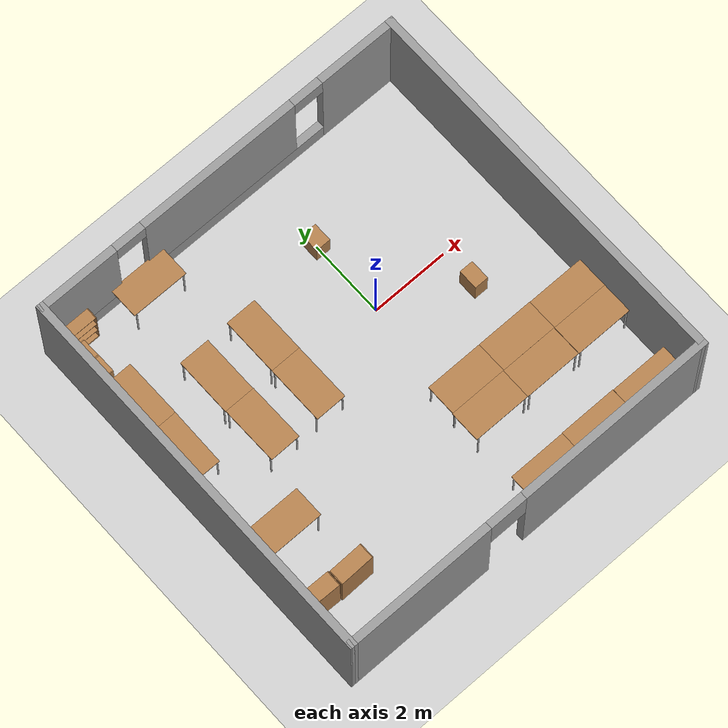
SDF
<sdf version="1.4">
 <world name="default">
  <model name="ground_plane">
   <static>1</static>
   <link name="link">
    <collision name="collision">
     <geometry><plane><normal>0 0 1</normal><size>100 100</size></plane></geometry>
     <surface><friction><ode><mu>100</mu><mu2>50</mu2></ode></friction></surface>
    </collision>
    <visual name="visual">
     <cast_shadows>0</cast_shadows>
     <geometry><plane><normal>0 0 1</normal><size>100 100</size></plane></geometry>
     <material>
      <script><uri>file://media/materials/scripts/gazebo.material</uri><name>Gazebo/Grey</name></script>
     </material>
    </visual>
    <velocity_decay><linear>0</linear><angular>0</angular></velocity_decay>
   </link>
  </model>
  <light name="sun" type="directional">
   <pose>0 0 10 0 -0 0</pose>
   <diffuse>0.8 0.8 0.8 1</diffuse>
   <specular>0.2 0.2 0.2 1</specular>
   <attenuation>
    <range>1000</range>
    <constant>0.9</constant>
    <linear>0.01</linear>
    <quadratic>0.001</quadratic>
   </attenuation>
   <direction>-0.5 0.1 -0.9</direction>
  </light>
  <physics type="ode">
   <max_step_size>0.001</max_step_size>
   <real_time_factor>1</real_time_factor>
   <real_time_update_rate>1000</real_time_update_rate>
   <gravity>0 0 -9.8</gravity>
  </physics>
  <scene><ambient>0.4 0.4 0.4 1</ambient><background>0.7 0.7 0.7 1</background><shadows>1</shadows></scene>
  <spherical_coordinates>
   <surface_model>EARTH_WGS84</surface_model>
   <latitude_deg>0</latitude_deg>
   <longitude_deg>0</longitude_deg>
   <elevation>0</elevation>
   <heading_deg>0</heading_deg>
  </spherical_coordinates>
  <model name="bookshelf">
   <static>1</static>
   <link name="link">
    <inertial><mass>1</mass></inertial>
    <collision name="back">
     <pose>0 0.005 0.6 0 -0 0</pose>
     <geometry><box><size>0.9 0.01 1.2</size></box></geometry>
    </collision>
    <visual name="visual1">
     <pose>0 0.005 0.6 0 -0 0</pose>
     <geometry><box><size>0.9 0.01 1.2</size></box></geometry>
     <material>
      <script><uri>file://media/materials/scripts/gazebo.material</uri><name>Gazebo/Wood</name></script>
     </material>
    </visual>
    <collision name="left_side">
     <pose>0.45 -0.195 0.6 0 -0 0</pose>
     <geometry><box><size>0.02 0.4 1.2</size></box></geometry>
    </collision>
    <visual name="visual2">
     <pose>0.45 -0.195 0.6 0 -0 0</pose>
     <geometry><box><size>0.02 0.4 1.2</size></box></geometry>
     <material>
      <script><uri>file://media/materials/scripts/gazebo.material</uri><name>Gazebo/Wood</name></script>
     </material>
    </visual>
    <collision name="right_side">
     <pose>-0.45 -0.195 0.6 0 -0 0</pose>
     <geometry><box><size>0.02 0.4 1.2</size></box></geometry>
    </collision>
    <visual name="visual3">
     <pose>-0.45 -0.195 0.6 0 -0 0</pose>
     <geometry><box><size>0.02 0.4 1.2</size></box></geometry>
     <material>
      <script><uri>file://media/materials/scripts/gazebo.material</uri><name>Gazebo/Wood</name></script>
     </material>
    </visual>
    <collision name="bottom">
     <pose>0 -0.195 0.03 0 -0 0</pose>
     <geometry><box><size>0.88 0.4 0.06</size></box></geometry>
    </collision>
    <visual name="visual4">
     <pose>0 -0.195 0.03 0 -0 0</pose>
     <geometry><box><size>0.88 0.4 0.06</size></box></geometry>
     <material>
      <script><uri>file://media/materials/scripts/gazebo.material</uri><name>Gazebo/Wood</name></script>
     </material>
    </visual>
    <collision name="top">
     <pose>0 -0.195 1.19 0 -0 0</pose>
     <geometry><box><size>0.88 0.4 0.02</size></box></geometry>
    </collision>
    <visual name="visual5">
     <pose>0 -0.195 1.19 0 -0 0</pose>
     <geometry><box><size>0.88 0.4 0.02</size></box></geometry>
     <material>
      <script><uri>file://media/materials/scripts/gazebo.material</uri><name>Gazebo/Wood</name></script>
     </material>
    </visual>
    <collision name="low_shelf">
     <pose>0 -0.195 0.43 0 -0 0</pose>
     <geometry><box><size>0.88 0.4 0.02</size></box></geometry>
    </collision>
    <visual name="visual6">
     <pose>0 -0.195 0.43 0 -0 0</pose>
     <geometry><box><size>0.88 0.4 0.02</size></box></geometry>
     <material>
      <script><uri>file://media/materials/scripts/gazebo.material</uri><name>Gazebo/Wood</name></script>
     </material>
    </visual>
    <collision name="high_shelf">
     <pose>0 -0.195 0.8 0 -0 0</pose>
     <geometry><box><size>0.88 0.4 0.02</size></box></geometry>
    </collision>
    <visual name="visual7">
     <pose>0 -0.195 0.8 0 -0 0</pose>
     <geometry><box><size>0.88 0.4 0.02</size></box></geometry>
     <material>
      <script><uri>file://media/materials/scripts/gazebo.material</uri><name>Gazebo/Wood</name></script>
     </material>
    </visual>
    <velocity_decay><linear>0</linear><angular>0</angular></velocity_decay>
   </link>
   <pose>-5.47897 -4.4727 0 0 -0 3.12502</pose>
  </model>
  <model name="bookshelf_0">
   <static>1</static>
   <link name="link">
    <inertial><mass>1</mass></inertial>
    <collision name="back">
     <pose>0 0.005 0.6 0 -0 0</pose>
     <geometry><box><size>0.9 0.01 1.2</size></box></geometry>
    </collision>
    <visual name="visual1">
     <pose>0 0.005 0.6 0 -0 0</pose>
     <geometry><box><size>0.9 0.01 1.2</size></box></geometry>
     <material>
      <script><uri>file://media/materials/scripts/gazebo.material</uri><name>Gazebo/Wood</name></script>
     </material>
    </visual>
    <collision name="left_side">
     <pose>0.45 -0.195 0.6 0 -0 0</pose>
     <geometry><box><size>0.02 0.4 1.2</size></box></geometry>
    </collision>
    <visual name="visual2">
     <pose>0.45 -0.195 0.6 0 -0 0</pose>
     <geometry><box><size>0.02 0.4 1.2</size></box></geometry>
     <material>
      <script><uri>file://media/materials/scripts/gazebo.material</uri><name>Gazebo/Wood</name></script>
     </material>
    </visual>
    <collision name="right_side">
     <pose>-0.45 -0.195 0.6 0 -0 0</pose>
     <geometry><box><size>0.02 0.4 1.2</size></box></geometry>
    </collision>
    <visual name="visual3">
     <pose>-0.45 -0.195 0.6 0 -0 0</pose>
     <geometry><box><size>0.02 0.4 1.2</size></box></geometry>
     <material>
      <script><uri>file://media/materials/scripts/gazebo.material</uri><name>Gazebo/Wood</name></script>
     </material>
    </visual>
    <collision name="bottom">
     <pose>0 -0.195 0.03 0 -0 0</pose>
     <geometry><box><size>0.88 0.4 0.06</size></box></geometry>
    </collision>
    <visual name="visual4">
     <pose>0 -0.195 0.03 0 -0 0</pose>
     <geometry><box><size>0.88 0.4 0.06</size></box></geometry>
     <material>
      <script><uri>file://media/materials/scripts/gazebo.material</uri><name>Gazebo/Wood</name></script>
     </material>
    </visual>
    <collision name="top">
     <pose>0 -0.195 1.19 0 -0 0</pose>
     <geometry><box><size>0.88 0.4 0.02</size></box></geometry>
    </collision>
    <visual name="visual5">
     <pose>0 -0.195 1.19 0 -0 0</pose>
     <geometry><box><size>0.88 0.4 0.02</size></box></geometry>
     <material>
      <script><uri>file://media/materials/scripts/gazebo.material</uri><name>Gazebo/Wood</name></script>
     </material>
    </visual>
    <collision name="low_shelf">
     <pose>0 -0.195 0.43 0 -0 0</pose>
     <geometry><box><size>0.88 0.4 0.02</size></box></geometry>
    </collision>
    <visual name="visual6">
     <pose>0 -0.195 0.43 0 -0 0</pose>
     <geometry><box><size>0.88 0.4 0.02</size></box></geometry>
     <material>
      <script><uri>file://media/materials/scripts/gazebo.material</uri><name>Gazebo/Wood</name></script>
     </material>
    </visual>
    <collision name="high_shelf">
     <pose>0 -0.195 0.8 0 -0 0</pose>
     <geometry><box><size>0.88 0.4 0.02</size></box></geometry>
    </collision>
    <visual name="visual7">
     <pose>0 -0.195 0.8 0 -0 0</pose>
     <geometry><box><size>0.88 0.4 0.02</size></box></geometry>
     <material>
      <script><uri>file://media/materials/scripts/gazebo.material</uri><name>Gazebo/Wood</name></script>
     </material>
    </visual>
    <velocity_decay><linear>0</linear><angular>0</angular></velocity_decay>
   </link>
   <pose>-4.5364 -4.49607 0 0 0 -3.12092</pose>
  </model>
  <model name="table">
   <static>1</static>
   <link name="link">
    <collision name="surface">
     <pose>0 0 1 0 -0 0</pose>
     <geometry><box><size>1.5 0.8 0.03</size></box></geometry>
     <surface><friction><ode><mu>0.6</mu><mu2>0.6</mu2></ode></friction></surface>
    </collision>
    <visual name="visual1">
     <pose>0 0 1 0 -0 0</pose>
     <geometry><box><size>1.5 0.8 0.03</size></box></geometry>
     <material>
      <script><uri>file://media/materials/scripts/gazebo.material</uri><name>Gazebo/Wood</name></script>
     </material>
    </visual>
    <collision name="front_left_leg">
     <pose>0.68 0.38 0.5 0 -0 0</pose>
     <geometry><cylinder><radius>0.02</radius><length>1</length></cylinder></geometry>
    </collision>
    <visual name="front_left_leg">
     <pose>0.68 0.38 0.5 0 -0 0</pose>
     <geometry><cylinder><radius>0.02</radius><length>1</length></cylinder></geometry>
     <material>
      <script><uri>file://media/materials/scripts/gazebo.material</uri><name>Gazebo/Grey</name></script>
     </material>
    </visual>
    <collision name="front_right_leg">
     <pose>0.68 -0.38 0.5 0 -0 0</pose>
     <geometry><cylinder><radius>0.02</radius><length>1</length></cylinder></geometry>
    </collision>
    <visual name="front_right_leg">
     <pose>0.68 -0.38 0.5 0 -0 0</pose>
     <geometry><cylinder><radius>0.02</radius><length>1</length></cylinder></geometry>
     <material>
      <script><uri>file://media/materials/scripts/gazebo.material</uri><name>Gazebo/Grey</name></script>
     </material>
    </visual>
    <collision name="back_right_leg">
     <pose>-0.68 -0.38 0.5 0 -0 0</pose>
     <geometry><cylinder><radius>0.02</radius><length>1</length></cylinder></geometry>
    </collision>
    <visual name="back_right_leg">
     <pose>-0.68 -0.38 0.5 0 -0 0</pose>
     <geometry><cylinder><radius>0.02</radius><length>1</length></cylinder></geometry>
     <material>
      <script><uri>file://media/materials/scripts/gazebo.material</uri><name>Gazebo/Grey</name></script>
     </material>
    </visual>
    <collision name="back_left_leg">
     <pose>-0.68 0.38 0.5 0 -0 0</pose>
     <geometry><cylinder><radius>0.02</radius><length>1</length></cylinder></geometry>
    </collision>
    <visual name="back_left_leg">
     <pose>-0.68 0.38 0.5 0 -0 0</pose>
     <geometry><cylinder><radius>0.02</radius><length>1</length></cylinder></geometry>
     <material>
      <script><uri>file://media/materials/scripts/gazebo.material</uri><name>Gazebo/Grey</name></script>
     </material>
    </visual>
    <velocity_decay><linear>0</linear><angular>0</angular></velocity_decay>
   </link>
   <pose>3.14958 -3.576 0 0 -0 0</pose>
  </model>
  <model name="table_0">
   <static>1</static>
   <link name="link">
    <collision name="surface">
     <pose>0 0 1 0 -0 0</pose>
     <geometry><box><size>1.5 0.8 0.03</size></box></geometry>
     <surface><friction><ode><mu>0.6</mu><mu2>0.6</mu2></ode></friction></surface>
    </collision>
    <visual name="visual1">
     <pose>0 0 1 0 -0 0</pose>
     <geometry><box><size>1.5 0.8 0.03</size></box></geometry>
     <material>
      <script><uri>file://media/materials/scripts/gazebo.material</uri><name>Gazebo/Wood</name></script>
     </material>
    </visual>
    <collision name="front_left_leg">
     <pose>0.68 0.38 0.5 0 -0 0</pose>
     <geometry><cylinder><radius>0.02</radius><length>1</length></cylinder></geometry>
    </collision>
    <visual name="front_left_leg">
     <pose>0.68 0.38 0.5 0 -0 0</pose>
     <geometry><cylinder><radius>0.02</radius><length>1</length></cylinder></geometry>
     <material>
      <script><uri>file://media/materials/scripts/gazebo.material</uri><name>Gazebo/Grey</name></script>
     </material>
    </visual>
    <collision name="front_right_leg">
     <pose>0.68 -0.38 0.5 0 -0 0</pose>
     <geometry><cylinder><radius>0.02</radius><length>1</length></cylinder></geometry>
    </collision>
    <visual name="front_right_leg">
     <pose>0.68 -0.38 0.5 0 -0 0</pose>
     <geometry><cylinder><radius>0.02</radius><length>1</length></cylinder></geometry>
     <material>
      <script><uri>file://media/materials/scripts/gazebo.material</uri><name>Gazebo/Grey</name></script>
     </material>
    </visual>
    <collision name="back_right_leg">
     <pose>-0.68 -0.38 0.5 0 -0 0</pose>
     <geometry><cylinder><radius>0.02</radius><length>1</length></cylinder></geometry>
    </collision>
    <visual name="back_right_leg">
     <pose>-0.68 -0.38 0.5 0 -0 0</pose>
     <geometry><cylinder><radius>0.02</radius><length>1</length></cylinder></geometry>
     <material>
      <script><uri>file://media/materials/scripts/gazebo.material</uri><name>Gazebo/Grey</name></script>
     </material>
    </visual>
    <collision name="back_left_leg">
     <pose>-0.68 0.38 0.5 0 -0 0</pose>
     <geometry><cylinder><radius>0.02</radius><length>1</length></cylinder></geometry>
    </collision>
    <visual name="back_left_leg">
     <pose>-0.68 0.38 0.5 0 -0 0</pose>
     <geometry><cylinder><radius>0.02</radius><length>1</length></cylinder></geometry>
     <material>
      <script><uri>file://media/materials/scripts/gazebo.material</uri><name>Gazebo/Grey</name></script>
     </material>
    </visual>
    <velocity_decay><linear>0</linear><angular>0</angular></velocity_decay>
   </link>
   <pose>3.15246 -2.77618 0 0 -0 0</pose>
  </model>
  <model name="table_1">
   <static>1</static>
   <link name="link">
    <collision name="surface">
     <pose>0 0 1 0 -0 0</pose>
     <geometry><box><size>1.5 0.8 0.03</size></box></geometry>
     <surface><friction><ode><mu>0.6</mu><mu2>0.6</mu2></ode></friction></surface>
    </collision>
    <visual name="visual1">
     <pose>0 0 1 0 -0 0</pose>
     <geometry><box><size>1.5 0.8 0.03</size></box></geometry>
     <material>
      <script><uri>file://media/materials/scripts/gazebo.material</uri><name>Gazebo/Wood</name></script>
     </material>
    </visual>
    <collision name="front_left_leg">
     <pose>0.68 0.38 0.5 0 -0 0</pose>
     <geometry><cylinder><radius>0.02</radius><length>1</length></cylinder></geometry>
    </collision>
    <visual name="front_left_leg">
     <pose>0.68 0.38 0.5 0 -0 0</pose>
     <geometry><cylinder><radius>0.02</radius><length>1</length></cylinder></geometry>
     <material>
      <script><uri>file://media/materials/scripts/gazebo.material</uri><name>Gazebo/Grey</name></script>
     </material>
    </visual>
    <collision name="front_right_leg">
     <pose>0.68 -0.38 0.5 0 -0 0</pose>
     <geometry><cylinder><radius>0.02</radius><length>1</length></cylinder></geometry>
    </collision>
    <visual name="front_right_leg">
     <pose>0.68 -0.38 0.5 0 -0 0</pose>
     <geometry><cylinder><radius>0.02</radius><length>1</length></cylinder></geometry>
     <material>
      <script><uri>file://media/materials/scripts/gazebo.material</uri><name>Gazebo/Grey</name></script>
     </material>
    </visual>
    <collision name="back_right_leg">
     <pose>-0.68 -0.38 0.5 0 -0 0</pose>
     <geometry><cylinder><radius>0.02</radius><length>1</length></cylinder></geometry>
    </collision>
    <visual name="back_right_leg">
     <pose>-0.68 -0.38 0.5 0 -0 0</pose>
     <geometry><cylinder><radius>0.02</radius><length>1</length></cylinder></geometry>
     <material>
      <script><uri>file://media/materials/scripts/gazebo.material</uri><name>Gazebo/Grey</name></script>
     </material>
    </visual>
    <collision name="back_left_leg">
     <pose>-0.68 0.38 0.5 0 -0 0</pose>
     <geometry><cylinder><radius>0.02</radius><length>1</length></cylinder></geometry>
    </collision>
    <visual name="back_left_leg">
     <pose>-0.68 0.38 0.5 0 -0 0</pose>
     <geometry><cylinder><radius>0.02</radius><length>1</length></cylinder></geometry>
     <material>
      <script><uri>file://media/materials/scripts/gazebo.material</uri><name>Gazebo/Grey</name></script>
     </material>
    </visual>
    <velocity_decay><linear>0</linear><angular>0</angular></velocity_decay>
   </link>
   <pose>1.64385 -3.57049 0 0 -0 0</pose>
  </model>
  <model name="table_2">
   <static>1</static>
   <link name="link">
    <collision name="surface">
     <pose>0 0 1 0 -0 0</pose>
     <geometry><box><size>1.5 0.8 0.03</size></box></geometry>
     <surface><friction><ode><mu>0.6</mu><mu2>0.6</mu2></ode></friction></surface>
    </collision>
    <visual name="visual1">
     <pose>0 0 1 0 -0 0</pose>
     <geometry><box><size>1.5 0.8 0.03</size></box></geometry>
     <material>
      <script><uri>file://media/materials/scripts/gazebo.material</uri><name>Gazebo/Wood</name></script>
     </material>
    </visual>
    <collision name="front_left_leg">
     <pose>0.68 0.38 0.5 0 -0 0</pose>
     <geometry><cylinder><radius>0.02</radius><length>1</length></cylinder></geometry>
    </collision>
    <visual name="front_left_leg">
     <pose>0.68 0.38 0.5 0 -0 0</pose>
     <geometry><cylinder><radius>0.02</radius><length>1</length></cylinder></geometry>
     <material>
      <script><uri>file://media/materials/scripts/gazebo.material</uri><name>Gazebo/Grey</name></script>
     </material>
    </visual>
    <collision name="front_right_leg">
     <pose>0.68 -0.38 0.5 0 -0 0</pose>
     <geometry><cylinder><radius>0.02</radius><length>1</length></cylinder></geometry>
    </collision>
    <visual name="front_right_leg">
     <pose>0.68 -0.38 0.5 0 -0 0</pose>
     <geometry><cylinder><radius>0.02</radius><length>1</length></cylinder></geometry>
     <material>
      <script><uri>file://media/materials/scripts/gazebo.material</uri><name>Gazebo/Grey</name></script>
     </material>
    </visual>
    <collision name="back_right_leg">
     <pose>-0.68 -0.38 0.5 0 -0 0</pose>
     <geometry><cylinder><radius>0.02</radius><length>1</length></cylinder></geometry>
    </collision>
    <visual name="back_right_leg">
     <pose>-0.68 -0.38 0.5 0 -0 0</pose>
     <geometry><cylinder><radius>0.02</radius><length>1</length></cylinder></geometry>
     <material>
      <script><uri>file://media/materials/scripts/gazebo.material</uri><name>Gazebo/Grey</name></script>
     </material>
    </visual>
    <collision name="back_left_leg">
     <pose>-0.68 0.38 0.5 0 -0 0</pose>
     <geometry><cylinder><radius>0.02</radius><length>1</length></cylinder></geometry>
    </collision>
    <visual name="back_left_leg">
     <pose>-0.68 0.38 0.5 0 -0 0</pose>
     <geometry><cylinder><radius>0.02</radius><length>1</length></cylinder></geometry>
     <material>
      <script><uri>file://media/materials/scripts/gazebo.material</uri><name>Gazebo/Grey</name></script>
     </material>
    </visual>
    <velocity_decay><linear>0</linear><angular>0</angular></velocity_decay>
   </link>
   <pose>1.65761 -2.77009 0 0 -0 0</pose>
  </model>
  <model name="table_3">
   <static>1</static>
   <link name="link">
    <collision name="surface">
     <pose>0 0 1 0 -0 0</pose>
     <geometry><box><size>1.5 0.8 0.03</size></box></geometry>
     <surface><friction><ode><mu>0.6</mu><mu2>0.6</mu2></ode></friction></surface>
    </collision>
    <visual name="visual1">
     <pose>0 0 1 0 -0 0</pose>
     <geometry><box><size>1.5 0.8 0.03</size></box></geometry>
     <material>
      <script><uri>file://media/materials/scripts/gazebo.material</uri><name>Gazebo/Wood</name></script>
     </material>
    </visual>
    <collision name="front_left_leg">
     <pose>0.68 0.38 0.5 0 -0 0</pose>
     <geometry><cylinder><radius>0.02</radius><length>1</length></cylinder></geometry>
    </collision>
    <visual name="front_left_leg">
     <pose>0.68 0.38 0.5 0 -0 0</pose>
     <geometry><cylinder><radius>0.02</radius><length>1</length></cylinder></geometry>
     <material>
      <script><uri>file://media/materials/scripts/gazebo.material</uri><name>Gazebo/Grey</name></script>
     </material>
    </visual>
    <collision name="front_right_leg">
     <pose>0.68 -0.38 0.5 0 -0 0</pose>
     <geometry><cylinder><radius>0.02</radius><length>1</length></cylinder></geometry>
    </collision>
    <visual name="front_right_leg">
     <pose>0.68 -0.38 0.5 0 -0 0</pose>
     <geometry><cylinder><radius>0.02</radius><length>1</length></cylinder></geometry>
     <material>
      <script><uri>file://media/materials/scripts/gazebo.material</uri><name>Gazebo/Grey</name></script>
     </material>
    </visual>
    <collision name="back_right_leg">
     <pose>-0.68 -0.38 0.5 0 -0 0</pose>
     <geometry><cylinder><radius>0.02</radius><length>1</length></cylinder></geometry>
    </collision>
    <visual name="back_right_leg">
     <pose>-0.68 -0.38 0.5 0 -0 0</pose>
     <geometry><cylinder><radius>0.02</radius><length>1</length></cylinder></geometry>
     <material>
      <script><uri>file://media/materials/scripts/gazebo.material</uri><name>Gazebo/Grey</name></script>
     </material>
    </visual>
    <collision name="back_left_leg">
     <pose>-0.68 0.38 0.5 0 -0 0</pose>
     <geometry><cylinder><radius>0.02</radius><length>1</length></cylinder></geometry>
    </collision>
    <visual name="back_left_leg">
     <pose>-0.68 0.38 0.5 0 -0 0</pose>
     <geometry><cylinder><radius>0.02</radius><length>1</length></cylinder></geometry>
     <material>
      <script><uri>file://media/materials/scripts/gazebo.material</uri><name>Gazebo/Grey</name></script>
     </material>
    </visual>
    <velocity_decay><linear>0</linear><angular>0</angular></velocity_decay>
   </link>
   <pose>0.147691 -3.56685 0 0 -0 0</pose>
  </model>
  <model name="table_4">
   <static>1</static>
   <link name="link">
    <collision name="surface">
     <pose>0 0 1 0 -0 0</pose>
     <geometry><box><size>1.5 0.8 0.03</size></box></geometry>
     <surface><friction><ode><mu>0.6</mu><mu2>0.6</mu2></ode></friction></surface>
    </collision>
    <visual name="visual1">
     <pose>0 0 1 0 -0 0</pose>
     <geometry><box><size>1.5 0.8 0.03</size></box></geometry>
     <material>
      <script><uri>file://media/materials/scripts/gazebo.material</uri><name>Gazebo/Wood</name></script>
     </material>
    </visual>
    <collision name="front_left_leg">
     <pose>0.68 0.38 0.5 0 -0 0</pose>
     <geometry><cylinder><radius>0.02</radius><length>1</length></cylinder></geometry>
    </collision>
    <visual name="front_left_leg">
     <pose>0.68 0.38 0.5 0 -0 0</pose>
     <geometry><cylinder><radius>0.02</radius><length>1</length></cylinder></geometry>
     <material>
      <script><uri>file://media/materials/scripts/gazebo.material</uri><name>Gazebo/Grey</name></script>
     </material>
    </visual>
    <collision name="front_right_leg">
     <pose>0.68 -0.38 0.5 0 -0 0</pose>
     <geometry><cylinder><radius>0.02</radius><length>1</length></cylinder></geometry>
    </collision>
    <visual name="front_right_leg">
     <pose>0.68 -0.38 0.5 0 -0 0</pose>
     <geometry><cylinder><radius>0.02</radius><length>1</length></cylinder></geometry>
     <material>
      <script><uri>file://media/materials/scripts/gazebo.material</uri><name>Gazebo/Grey</name></script>
     </material>
    </visual>
    <collision name="back_right_leg">
     <pose>-0.68 -0.38 0.5 0 -0 0</pose>
     <geometry><cylinder><radius>0.02</radius><length>1</length></cylinder></geometry>
    </collision>
    <visual name="back_right_leg">
     <pose>-0.68 -0.38 0.5 0 -0 0</pose>
     <geometry><cylinder><radius>0.02</radius><length>1</length></cylinder></geometry>
     <material>
      <script><uri>file://media/materials/scripts/gazebo.material</uri><name>Gazebo/Grey</name></script>
     </material>
    </visual>
    <collision name="back_left_leg">
     <pose>-0.68 0.38 0.5 0 -0 0</pose>
     <geometry><cylinder><radius>0.02</radius><length>1</length></cylinder></geometry>
    </collision>
    <visual name="back_left_leg">
     <pose>-0.68 0.38 0.5 0 -0 0</pose>
     <geometry><cylinder><radius>0.02</radius><length>1</length></cylinder></geometry>
     <material>
      <script><uri>file://media/materials/scripts/gazebo.material</uri><name>Gazebo/Grey</name></script>
     </material>
    </visual>
    <velocity_decay><linear>0</linear><angular>0</angular></velocity_decay>
   </link>
   <pose>0.166165 -2.77151 0 0 -0 0</pose>
  </model>
  <model name="table_5">
   <static>1</static>
   <link name="link">
    <collision name="surface">
     <pose>0 0 1 0 -0 0</pose>
     <geometry><box><size>1.5 0.8 0.03</size></box></geometry>
     <surface><friction><ode><mu>0.6</mu><mu2>0.6</mu2></ode></friction></surface>
    </collision>
    <visual name="visual1">
     <pose>0 0 1 0 -0 0</pose>
     <geometry><box><size>1.5 0.8 0.03</size></box></geometry>
     <material>
      <script><uri>file://media/materials/scripts/gazebo.material</uri><name>Gazebo/Wood</name></script>
     </material>
    </visual>
    <collision name="front_left_leg">
     <pose>0.68 0.38 0.5 0 -0 0</pose>
     <geometry><cylinder><radius>0.02</radius><length>1</length></cylinder></geometry>
    </collision>
    <visual name="front_left_leg">
     <pose>0.68 0.38 0.5 0 -0 0</pose>
     <geometry><cylinder><radius>0.02</radius><length>1</length></cylinder></geometry>
     <material>
      <script><uri>file://media/materials/scripts/gazebo.material</uri><name>Gazebo/Grey</name></script>
     </material>
    </visual>
    <collision name="front_right_leg">
     <pose>0.68 -0.38 0.5 0 -0 0</pose>
     <geometry><cylinder><radius>0.02</radius><length>1</length></cylinder></geometry>
    </collision>
    <visual name="front_right_leg">
     <pose>0.68 -0.38 0.5 0 -0 0</pose>
     <geometry><cylinder><radius>0.02</radius><length>1</length></cylinder></geometry>
     <material>
      <script><uri>file://media/materials/scripts/gazebo.material</uri><name>Gazebo/Grey</name></script>
     </material>
    </visual>
    <collision name="back_right_leg">
     <pose>-0.68 -0.38 0.5 0 -0 0</pose>
     <geometry><cylinder><radius>0.02</radius><length>1</length></cylinder></geometry>
    </collision>
    <visual name="back_right_leg">
     <pose>-0.68 -0.38 0.5 0 -0 0</pose>
     <geometry><cylinder><radius>0.02</radius><length>1</length></cylinder></geometry>
     <material>
      <script><uri>file://media/materials/scripts/gazebo.material</uri><name>Gazebo/Grey</name></script>
     </material>
    </visual>
    <collision name="back_left_leg">
     <pose>-0.68 0.38 0.5 0 -0 0</pose>
     <geometry><cylinder><radius>0.02</radius><length>1</length></cylinder></geometry>
    </collision>
    <visual name="back_left_leg">
     <pose>-0.68 0.38 0.5 0 -0 0</pose>
     <geometry><cylinder><radius>0.02</radius><length>1</length></cylinder></geometry>
     <material>
      <script><uri>file://media/materials/scripts/gazebo.material</uri><name>Gazebo/Grey</name></script>
     </material>
    </visual>
    <velocity_decay><linear>0</linear><angular>0</angular></velocity_decay>
   </link>
   <pose>3.13696 -5.4898 0 0 -0 0</pose>
  </model>
  <model name="table_6">
   <static>1</static>
   <link name="link">
    <collision name="surface">
     <pose>0 0 1 0 -0 0</pose>
     <geometry><box><size>1.5 0.8 0.03</size></box></geometry>
     <surface><friction><ode><mu>0.6</mu><mu2>0.6</mu2></ode></friction></surface>
    </collision>
    <visual name="visual1">
     <pose>0 0 1 0 -0 0</pose>
     <geometry><box><size>1.5 0.8 0.03</size></box></geometry>
     <material>
      <script><uri>file://media/materials/scripts/gazebo.material</uri><name>Gazebo/Wood</name></script>
     </material>
    </visual>
    <collision name="front_left_leg">
     <pose>0.68 0.38 0.5 0 -0 0</pose>
     <geometry><cylinder><radius>0.02</radius><length>1</length></cylinder></geometry>
    </collision>
    <visual name="front_left_leg">
     <pose>0.68 0.38 0.5 0 -0 0</pose>
     <geometry><cylinder><radius>0.02</radius><length>1</length></cylinder></geometry>
     <material>
      <script><uri>file://media/materials/scripts/gazebo.material</uri><name>Gazebo/Grey</name></script>
     </material>
    </visual>
    <collision name="front_right_leg">
     <pose>0.68 -0.38 0.5 0 -0 0</pose>
     <geometry><cylinder><radius>0.02</radius><length>1</length></cylinder></geometry>
    </collision>
    <visual name="front_right_leg">
     <pose>0.68 -0.38 0.5 0 -0 0</pose>
     <geometry><cylinder><radius>0.02</radius><length>1</length></cylinder></geometry>
     <material>
      <script><uri>file://media/materials/scripts/gazebo.material</uri><name>Gazebo/Grey</name></script>
     </material>
    </visual>
    <collision name="back_right_leg">
     <pose>-0.68 -0.38 0.5 0 -0 0</pose>
     <geometry><cylinder><radius>0.02</radius><length>1</length></cylinder></geometry>
    </collision>
    <visual name="back_right_leg">
     <pose>-0.68 -0.38 0.5 0 -0 0</pose>
     <geometry><cylinder><radius>0.02</radius><length>1</length></cylinder></geometry>
     <material>
      <script><uri>file://media/materials/scripts/gazebo.material</uri><name>Gazebo/Grey</name></script>
     </material>
    </visual>
    <collision name="back_left_leg">
     <pose>-0.68 0.38 0.5 0 -0 0</pose>
     <geometry><cylinder><radius>0.02</radius><length>1</length></cylinder></geometry>
    </collision>
    <visual name="back_left_leg">
     <pose>-0.68 0.38 0.5 0 -0 0</pose>
     <geometry><cylinder><radius>0.02</radius><length>1</length></cylinder></geometry>
     <material>
      <script><uri>file://media/materials/scripts/gazebo.material</uri><name>Gazebo/Grey</name></script>
     </material>
    </visual>
    <velocity_decay><linear>0</linear><angular>0</angular></velocity_decay>
   </link>
   <pose>1.63488 -5.47778 0 0 -0 0</pose>
  </model>
  <model name="table_7">
   <static>1</static>
   <link name="link">
    <collision name="surface">
     <pose>0 0 1 0 -0 0</pose>
     <geometry><box><size>1.5 0.8 0.03</size></box></geometry>
     <surface><friction><ode><mu>0.6</mu><mu2>0.6</mu2></ode></friction></surface>
    </collision>
    <visual name="visual1">
     <pose>0 0 1 0 -0 0</pose>
     <geometry><box><size>1.5 0.8 0.03</size></box></geometry>
     <material>
      <script><uri>file://media/materials/scripts/gazebo.material</uri><name>Gazebo/Wood</name></script>
     </material>
    </visual>
    <collision name="front_left_leg">
     <pose>0.68 0.38 0.5 0 -0 0</pose>
     <geometry><cylinder><radius>0.02</radius><length>1</length></cylinder></geometry>
    </collision>
    <visual name="front_left_leg">
     <pose>0.68 0.38 0.5 0 -0 0</pose>
     <geometry><cylinder><radius>0.02</radius><length>1</length></cylinder></geometry>
     <material>
      <script><uri>file://media/materials/scripts/gazebo.material</uri><name>Gazebo/Grey</name></script>
     </material>
    </visual>
    <collision name="front_right_leg">
     <pose>0.68 -0.38 0.5 0 -0 0</pose>
     <geometry><cylinder><radius>0.02</radius><length>1</length></cylinder></geometry>
    </collision>
    <visual name="front_right_leg">
     <pose>0.68 -0.38 0.5 0 -0 0</pose>
     <geometry><cylinder><radius>0.02</radius><length>1</length></cylinder></geometry>
     <material>
      <script><uri>file://media/materials/scripts/gazebo.material</uri><name>Gazebo/Grey</name></script>
     </material>
    </visual>
    <collision name="back_right_leg">
     <pose>-0.68 -0.38 0.5 0 -0 0</pose>
     <geometry><cylinder><radius>0.02</radius><length>1</length></cylinder></geometry>
    </collision>
    <visual name="back_right_leg">
     <pose>-0.68 -0.38 0.5 0 -0 0</pose>
     <geometry><cylinder><radius>0.02</radius><length>1</length></cylinder></geometry>
     <material>
      <script><uri>file://media/materials/scripts/gazebo.material</uri><name>Gazebo/Grey</name></script>
     </material>
    </visual>
    <collision name="back_left_leg">
     <pose>-0.68 0.38 0.5 0 -0 0</pose>
     <geometry><cylinder><radius>0.02</radius><length>1</length></cylinder></geometry>
    </collision>
    <visual name="back_left_leg">
     <pose>-0.68 0.38 0.5 0 -0 0</pose>
     <geometry><cylinder><radius>0.02</radius><length>1</length></cylinder></geometry>
     <material>
      <script><uri>file://media/materials/scripts/gazebo.material</uri><name>Gazebo/Grey</name></script>
     </material>
    </visual>
    <velocity_decay><linear>0</linear><angular>0</angular></velocity_decay>
   </link>
   <pose>0.143295 -5.48733 0 0 -0 0</pose>
  </model>
  <model name="cabinet">
   <static>1</static>
   <link name="cabinet_bottom_plate">
    <inertial>
     <pose>0 0 -1 0 -0 0</pose>
     <inertia><ixx>2.05</ixx><ixy>0</ixy><ixz>0</ixz><iyy>2.05</iyy><iyz>0</iyz><izz>2.05</izz></inertia>
     <mass>25</mass>
    </inertial>
    <collision name="cabinet_bottom_plate_geom">
     <pose>0 0 0.01 0 -0 0</pose>
     <geometry><box><size>0.45 0.45 0.02</size></box></geometry>
    </collision>
    <visual name="cabinet_bottom_plate_geom_visual">
     <pose>0 0 0.01 0 -0 0</pose>
     <geometry><box><size>0.45 0.45 0.02</size></box></geometry>
     <material>
      <script><uri>file://media/materials/scripts/gazebo.material</uri><name>Gazebo/Wood</name></script>
     </material>
    </visual>
    <collision name="cabinet_bottom_plate_geom_cabinet_back_plate">
     <pose>0.235 0 0.51 0 -0 0</pose>
     <geometry><box><size>0.02 0.45 1.02</size></box></geometry>
    </collision>
    <visual name="cabinet_bottom_plate_geom_cabinet_back_plate_visual">
     <pose>0.235 0 0.51 0 -0 0</pose>
     <geometry><box><size>0.02 0.45 1.02</size></box></geometry>
     <material>
      <script><uri>file://media/materials/scripts/gazebo.material</uri><name>Gazebo/Wood</name></script>
     </material>
    </visual>
    <collision name="cabinet_bottom_plate_geom_cabinet_left_plate">
     <pose>0 0.235 0.51 0 -0 0</pose>
     <geometry><box><size>0.45 0.02 1.02</size></box></geometry>
    </collision>
    <visual name="cabinet_bottom_plate_geom_cabinet_left_plate_visual">
     <pose>0 0.235 0.51 0 -0 0</pose>
     <geometry><box><size>0.45 0.02 1.02</size></box></geometry>
     <material>
      <script><uri>file://media/materials/scripts/gazebo.material</uri><name>Gazebo/Wood</name></script>
     </material>
    </visual>
    <collision name="cabinet_bottom_plate_geom_cabinet_middle_plate">
     <pose>0 0 0.51 0 -0 0</pose>
     <geometry><box><size>0.45 0.45 0.02</size></box></geometry>
    </collision>
    <visual name="cabinet_bottom_plate_geom_cabinet_middle_plate_visual">
     <pose>0 0 0.51 0 -0 0</pose>
     <geometry><box><size>0.45 0.45 0.02</size></box></geometry>
     <material>
      <script><uri>file://media/materials/scripts/gazebo.material</uri><name>Gazebo/Wood</name></script>
     </material>
    </visual>
    <collision name="cabinet_bottom_plate_geom_cabinet_right_plate">
     <pose>0 -0.235 0.51 0 -0 0</pose>
     <geometry><box><size>0.45 0.02 1.02</size></box></geometry>
    </collision>
    <visual name="cabinet_bottom_plate_geom_cabinet_right_plate_visual">
     <pose>0 -0.235 0.51 0 -0 0</pose>
     <geometry><box><size>0.45 0.02 1.02</size></box></geometry>
     <material>
      <script><uri>file://media/materials/scripts/gazebo.material</uri><name>Gazebo/Wood</name></script>
     </material>
    </visual>
    <collision name="cabinet_bottom_plate_geom_cabinet_top_plate">
     <pose>0 0 1.01 0 -0 0</pose>
     <geometry><box><size>0.45 0.45 0.02</size></box></geometry>
    </collision>
    <visual name="cabinet_bottom_plate_geom_cabinet_top_plate_visual">
     <pose>0 0 1.01 0 -0 0</pose>
     <geometry><box><size>0.45 0.45 0.02</size></box></geometry>
     <material>
      <script><uri>file://media/materials/scripts/gazebo.material</uri><name>Gazebo/Wood</name></script>
     </material>
    </visual>
    <velocity_decay><linear>0</linear><angular>0</angular></velocity_decay>
   </link>
   <pose>-5.69724 3.21191 0 0 0 -3.12456</pose>
  </model>
  <model name="cabinet_0">
   <static>1</static>
   <link name="cabinet_bottom_plate">
    <inertial>
     <pose>0 0 -1 0 -0 0</pose>
     <inertia><ixx>2.05</ixx><ixy>0</ixy><ixz>0</ixz><iyy>2.05</iyy><iyz>0</iyz><izz>2.05</izz></inertia>
     <mass>25</mass>
    </inertial>
    <collision name="cabinet_bottom_plate_geom">
     <pose>0 0 0.01 0 -0 0</pose>
     <geometry><box><size>0.45 0.45 0.02</size></box></geometry>
    </collision>
    <visual name="cabinet_bottom_plate_geom_visual">
     <pose>0 0 0.01 0 -0 0</pose>
     <geometry><box><size>0.45 0.45 0.02</size></box></geometry>
     <material>
      <script><uri>file://media/materials/scripts/gazebo.material</uri><name>Gazebo/Wood</name></script>
     </material>
    </visual>
    <collision name="cabinet_bottom_plate_geom_cabinet_back_plate">
     <pose>0.235 0 0.51 0 -0 0</pose>
     <geometry><box><size>0.02 0.45 1.02</size></box></geometry>
    </collision>
    <visual name="cabinet_bottom_plate_geom_cabinet_back_plate_visual">
     <pose>0.235 0 0.51 0 -0 0</pose>
     <geometry><box><size>0.02 0.45 1.02</size></box></geometry>
     <material>
      <script><uri>file://media/materials/scripts/gazebo.material</uri><name>Gazebo/Wood</name></script>
     </material>
    </visual>
    <collision name="cabinet_bottom_plate_geom_cabinet_left_plate">
     <pose>0 0.235 0.51 0 -0 0</pose>
     <geometry><box><size>0.45 0.02 1.02</size></box></geometry>
    </collision>
    <visual name="cabinet_bottom_plate_geom_cabinet_left_plate_visual">
     <pose>0 0.235 0.51 0 -0 0</pose>
     <geometry><box><size>0.45 0.02 1.02</size></box></geometry>
     <material>
      <script><uri>file://media/materials/scripts/gazebo.material</uri><name>Gazebo/Wood</name></script>
     </material>
    </visual>
    <collision name="cabinet_bottom_plate_geom_cabinet_middle_plate">
     <pose>0 0 0.51 0 -0 0</pose>
     <geometry><box><size>0.45 0.45 0.02</size></box></geometry>
    </collision>
    <visual name="cabinet_bottom_plate_geom_cabinet_middle_plate_visual">
     <pose>0 0 0.51 0 -0 0</pose>
     <geometry><box><size>0.45 0.45 0.02</size></box></geometry>
     <material>
      <script><uri>file://media/materials/scripts/gazebo.material</uri><name>Gazebo/Wood</name></script>
     </material>
    </visual>
    <collision name="cabinet_bottom_plate_geom_cabinet_right_plate">
     <pose>0 -0.235 0.51 0 -0 0</pose>
     <geometry><box><size>0.45 0.02 1.02</size></box></geometry>
    </collision>
    <visual name="cabinet_bottom_plate_geom_cabinet_right_plate_visual">
     <pose>0 -0.235 0.51 0 -0 0</pose>
     <geometry><box><size>0.45 0.02 1.02</size></box></geometry>
     <material>
      <script><uri>file://media/materials/scripts/gazebo.material</uri><name>Gazebo/Wood</name></script>
     </material>
    </visual>
    <collision name="cabinet_bottom_plate_geom_cabinet_top_plate">
     <pose>0 0 1.01 0 -0 0</pose>
     <geometry><box><size>0.45 0.45 0.02</size></box></geometry>
    </collision>
    <visual name="cabinet_bottom_plate_geom_cabinet_top_plate_visual">
     <pose>0 0 1.01 0 -0 0</pose>
     <geometry><box><size>0.45 0.45 0.02</size></box></geometry>
     <material>
      <script><uri>file://media/materials/scripts/gazebo.material</uri><name>Gazebo/Wood</name></script>
     </material>
    </visual>
    <velocity_decay><linear>0</linear><angular>0</angular></velocity_decay>
   </link>
   <pose>-5.68738 2.72419 0 0 0 -3.13777</pose>
  </model>
  <model name="bookshelf_1">
   <static>1</static>
   <link name="link">
    <inertial><mass>1</mass></inertial>
    <collision name="back">
     <pose>0 0.005 0.6 0 -0 0</pose>
     <geometry><box><size>0.9 0.01 1.2</size></box></geometry>
    </collision>
    <visual name="visual1">
     <pose>0 0.005 0.6 0 -0 0</pose>
     <geometry><box><size>0.9 0.01 1.2</size></box></geometry>
     <material>
      <script><uri>file://media/materials/scripts/gazebo.material</uri><name>Gazebo/Wood</name></script>
     </material>
    </visual>
    <collision name="left_side">
     <pose>0.45 -0.195 0.6 0 -0 0</pose>
     <geometry><box><size>0.02 0.4 1.2</size></box></geometry>
    </collision>
    <visual name="visual2">
     <pose>0.45 -0.195 0.6 0 -0 0</pose>
     <geometry><box><size>0.02 0.4 1.2</size></box></geometry>
     <material>
      <script><uri>file://media/materials/scripts/gazebo.material</uri><name>Gazebo/Wood</name></script>
     </material>
    </visual>
    <collision name="right_side">
     <pose>-0.45 -0.195 0.6 0 -0 0</pose>
     <geometry><box><size>0.02 0.4 1.2</size></box></geometry>
    </collision>
    <visual name="visual3">
     <pose>-0.45 -0.195 0.6 0 -0 0</pose>
     <geometry><box><size>0.02 0.4 1.2</size></box></geometry>
     <material>
      <script><uri>file://media/materials/scripts/gazebo.material</uri><name>Gazebo/Wood</name></script>
     </material>
    </visual>
    <collision name="bottom">
     <pose>0 -0.195 0.03 0 -0 0</pose>
     <geometry><box><size>0.88 0.4 0.06</size></box></geometry>
    </collision>
    <visual name="visual4">
     <pose>0 -0.195 0.03 0 -0 0</pose>
     <geometry><box><size>0.88 0.4 0.06</size></box></geometry>
     <material>
      <script><uri>file://media/materials/scripts/gazebo.material</uri><name>Gazebo/Wood</name></script>
     </material>
    </visual>
    <collision name="top">
     <pose>0 -0.195 1.19 0 -0 0</pose>
     <geometry><box><size>0.88 0.4 0.02</size></box></geometry>
    </collision>
    <visual name="visual5">
     <pose>0 -0.195 1.19 0 -0 0</pose>
     <geometry><box><size>0.88 0.4 0.02</size></box></geometry>
     <material>
      <script><uri>file://media/materials/scripts/gazebo.material</uri><name>Gazebo/Wood</name></script>
     </material>
    </visual>
    <collision name="low_shelf">
     <pose>0 -0.195 0.43 0 -0 0</pose>
     <geometry><box><size>0.88 0.4 0.02</size></box></geometry>
    </collision>
    <visual name="visual6">
     <pose>0 -0.195 0.43 0 -0 0</pose>
     <geometry><box><size>0.88 0.4 0.02</size></box></geometry>
     <material>
      <script><uri>file://media/materials/scripts/gazebo.material</uri><name>Gazebo/Wood</name></script>
     </material>
    </visual>
    <collision name="high_shelf">
     <pose>0 -0.195 0.8 0 -0 0</pose>
     <geometry><box><size>0.88 0.4 0.02</size></box></geometry>
    </collision>
    <visual name="visual7">
     <pose>0 -0.195 0.8 0 -0 0</pose>
     <geometry><box><size>0.88 0.4 0.02</size></box></geometry>
     <material>
      <script><uri>file://media/materials/scripts/gazebo.material</uri><name>Gazebo/Wood</name></script>
     </material>
    </visual>
    <velocity_decay><linear>0</linear><angular>0</angular></velocity_decay>
   </link>
   <pose>-5.43168 4 0 0 -0 0</pose>
  </model>
  <model name="table_8">
   <static>1</static>
   <link name="link">
    <collision name="surface">
     <pose>0 0 1 0 -0 0</pose>
     <geometry><box><size>1.5 0.8 0.03</size></box></geometry>
     <surface><friction><ode><mu>0.6</mu><mu2>0.6</mu2></ode></friction></surface>
    </collision>
    <visual name="visual1">
     <pose>0 0 1 0 -0 0</pose>
     <geometry><box><size>1.5 0.8 0.03</size></box></geometry>
     <material>
      <script><uri>file://media/materials/scripts/gazebo.material</uri><name>Gazebo/Wood</name></script>
     </material>
    </visual>
    <collision name="front_left_leg">
     <pose>0.68 0.38 0.5 0 -0 0</pose>
     <geometry><cylinder><radius>0.02</radius><length>1</length></cylinder></geometry>
    </collision>
    <visual name="front_left_leg">
     <pose>0.68 0.38 0.5 0 -0 0</pose>
     <geometry><cylinder><radius>0.02</radius><length>1</length></cylinder></geometry>
     <material>
      <script><uri>file://media/materials/scripts/gazebo.material</uri><name>Gazebo/Grey</name></script>
     </material>
    </visual>
    <collision name="front_right_leg">
     <pose>0.68 -0.38 0.5 0 -0 0</pose>
     <geometry><cylinder><radius>0.02</radius><length>1</length></cylinder></geometry>
    </collision>
    <visual name="front_right_leg">
     <pose>0.68 -0.38 0.5 0 -0 0</pose>
     <geometry><cylinder><radius>0.02</radius><length>1</length></cylinder></geometry>
     <material>
      <script><uri>file://media/materials/scripts/gazebo.material</uri><name>Gazebo/Grey</name></script>
     </material>
    </visual>
    <collision name="back_right_leg">
     <pose>-0.68 -0.38 0.5 0 -0 0</pose>
     <geometry><cylinder><radius>0.02</radius><length>1</length></cylinder></geometry>
    </collision>
    <visual name="back_right_leg">
     <pose>-0.68 -0.38 0.5 0 -0 0</pose>
     <geometry><cylinder><radius>0.02</radius><length>1</length></cylinder></geometry>
     <material>
      <script><uri>file://media/materials/scripts/gazebo.material</uri><name>Gazebo/Grey</name></script>
     </material>
    </visual>
    <collision name="back_left_leg">
     <pose>-0.68 0.38 0.5 0 -0 0</pose>
     <geometry><cylinder><radius>0.02</radius><length>1</length></cylinder></geometry>
    </collision>
    <visual name="back_left_leg">
     <pose>-0.68 0.38 0.5 0 -0 0</pose>
     <geometry><cylinder><radius>0.02</radius><length>1</length></cylinder></geometry>
     <material>
      <script><uri>file://media/materials/scripts/gazebo.material</uri><name>Gazebo/Grey</name></script>
     </material>
    </visual>
    <velocity_decay><linear>0</linear><angular>0</angular></velocity_decay>
   </link>
   <pose>-3.53797 3.54064 0 0 -0 0</pose>
  </model>
  <model name="table_9">
   <static>1</static>
   <link name="link">
    <collision name="surface">
     <pose>0 0 1 0 -0 0</pose>
     <geometry><box><size>1.5 0.8 0.03</size></box></geometry>
     <surface><friction><ode><mu>0.6</mu><mu2>0.6</mu2></ode></friction></surface>
    </collision>
    <visual name="visual1">
     <pose>0 0 1 0 -0 0</pose>
     <geometry><box><size>1.5 0.8 0.03</size></box></geometry>
     <material>
      <script><uri>file://media/materials/scripts/gazebo.material</uri><name>Gazebo/Wood</name></script>
     </material>
    </visual>
    <collision name="front_left_leg">
     <pose>0.68 0.38 0.5 0 -0 0</pose>
     <geometry><cylinder><radius>0.02</radius><length>1</length></cylinder></geometry>
    </collision>
    <visual name="front_left_leg">
     <pose>0.68 0.38 0.5 0 -0 0</pose>
     <geometry><cylinder><radius>0.02</radius><length>1</length></cylinder></geometry>
     <material>
      <script><uri>file://media/materials/scripts/gazebo.material</uri><name>Gazebo/Grey</name></script>
     </material>
    </visual>
    <collision name="front_right_leg">
     <pose>0.68 -0.38 0.5 0 -0 0</pose>
     <geometry><cylinder><radius>0.02</radius><length>1</length></cylinder></geometry>
    </collision>
    <visual name="front_right_leg">
     <pose>0.68 -0.38 0.5 0 -0 0</pose>
     <geometry><cylinder><radius>0.02</radius><length>1</length></cylinder></geometry>
     <material>
      <script><uri>file://media/materials/scripts/gazebo.material</uri><name>Gazebo/Grey</name></script>
     </material>
    </visual>
    <collision name="back_right_leg">
     <pose>-0.68 -0.38 0.5 0 -0 0</pose>
     <geometry><cylinder><radius>0.02</radius><length>1</length></cylinder></geometry>
    </collision>
    <visual name="back_right_leg">
     <pose>-0.68 -0.38 0.5 0 -0 0</pose>
     <geometry><cylinder><radius>0.02</radius><length>1</length></cylinder></geometry>
     <material>
      <script><uri>file://media/materials/scripts/gazebo.material</uri><name>Gazebo/Grey</name></script>
     </material>
    </visual>
    <collision name="back_left_leg">
     <pose>-0.68 0.38 0.5 0 -0 0</pose>
     <geometry><cylinder><radius>0.02</radius><length>1</length></cylinder></geometry>
    </collision>
    <visual name="back_left_leg">
     <pose>-0.68 0.38 0.5 0 -0 0</pose>
     <geometry><cylinder><radius>0.02</radius><length>1</length></cylinder></geometry>
     <material>
      <script><uri>file://media/materials/scripts/gazebo.material</uri><name>Gazebo/Grey</name></script>
     </material>
    </visual>
    <velocity_decay><linear>0</linear><angular>0</angular></velocity_decay>
   </link>
   <pose>-2.48045 0.921497 0 0 0 -1.56751</pose>
  </model>
  <model name="table_10">
   <static>1</static>
   <link name="link">
    <collision name="surface">
     <pose>0 0 1 0 -0 0</pose>
     <geometry><box><size>1.5 0.8 0.03</size></box></geometry>
     <surface><friction><ode><mu>0.6</mu><mu2>0.6</mu2></ode></friction></surface>
    </collision>
    <visual name="visual1">
     <pose>0 0 1 0 -0 0</pose>
     <geometry><box><size>1.5 0.8 0.03</size></box></geometry>
     <material>
      <script><uri>file://media/materials/scripts/gazebo.material</uri><name>Gazebo/Wood</name></script>
     </material>
    </visual>
    <collision name="front_left_leg">
     <pose>0.68 0.38 0.5 0 -0 0</pose>
     <geometry><cylinder><radius>0.02</radius><length>1</length></cylinder></geometry>
    </collision>
    <visual name="front_left_leg">
     <pose>0.68 0.38 0.5 0 -0 0</pose>
     <geometry><cylinder><radius>0.02</radius><length>1</length></cylinder></geometry>
     <material>
      <script><uri>file://media/materials/scripts/gazebo.material</uri><name>Gazebo/Grey</name></script>
     </material>
    </visual>
    <collision name="front_right_leg">
     <pose>0.68 -0.38 0.5 0 -0 0</pose>
     <geometry><cylinder><radius>0.02</radius><length>1</length></cylinder></geometry>
    </collision>
    <visual name="front_right_leg">
     <pose>0.68 -0.38 0.5 0 -0 0</pose>
     <geometry><cylinder><radius>0.02</radius><length>1</length></cylinder></geometry>
     <material>
      <script><uri>file://media/materials/scripts/gazebo.material</uri><name>Gazebo/Grey</name></script>
     </material>
    </visual>
    <collision name="back_right_leg">
     <pose>-0.68 -0.38 0.5 0 -0 0</pose>
     <geometry><cylinder><radius>0.02</radius><length>1</length></cylinder></geometry>
    </collision>
    <visual name="back_right_leg">
     <pose>-0.68 -0.38 0.5 0 -0 0</pose>
     <geometry><cylinder><radius>0.02</radius><length>1</length></cylinder></geometry>
     <material>
      <script><uri>file://media/materials/scripts/gazebo.material</uri><name>Gazebo/Grey</name></script>
     </material>
    </visual>
    <collision name="back_left_leg">
     <pose>-0.68 0.38 0.5 0 -0 0</pose>
     <geometry><cylinder><radius>0.02</radius><length>1</length></cylinder></geometry>
    </collision>
    <visual name="back_left_leg">
     <pose>-0.68 0.38 0.5 0 -0 0</pose>
     <geometry><cylinder><radius>0.02</radius><length>1</length></cylinder></geometry>
     <material>
      <script><uri>file://media/materials/scripts/gazebo.material</uri><name>Gazebo/Grey</name></script>
     </material>
    </visual>
    <velocity_decay><linear>0</linear><angular>0</angular></velocity_decay>
   </link>
   <pose>-2.47594 -0.565495 0 0 0 -1.56582</pose>
  </model>
  <model name="table_11">
   <static>1</static>
   <link name="link">
    <collision name="surface">
     <pose>0 0 1 0 -0 0</pose>
     <geometry><box><size>1.5 0.8 0.03</size></box></geometry>
     <surface><friction><ode><mu>0.6</mu><mu2>0.6</mu2></ode></friction></surface>
    </collision>
    <visual name="visual1">
     <pose>0 0 1 0 -0 0</pose>
     <geometry><box><size>1.5 0.8 0.03</size></box></geometry>
     <material>
      <script><uri>file://media/materials/scripts/gazebo.material</uri><name>Gazebo/Wood</name></script>
     </material>
    </visual>
    <collision name="front_left_leg">
     <pose>0.68 0.38 0.5 0 -0 0</pose>
     <geometry><cylinder><radius>0.02</radius><length>1</length></cylinder></geometry>
    </collision>
    <visual name="front_left_leg">
     <pose>0.68 0.38 0.5 0 -0 0</pose>
     <geometry><cylinder><radius>0.02</radius><length>1</length></cylinder></geometry>
     <material>
      <script><uri>file://media/materials/scripts/gazebo.material</uri><name>Gazebo/Grey</name></script>
     </material>
    </visual>
    <collision name="front_right_leg">
     <pose>0.68 -0.38 0.5 0 -0 0</pose>
     <geometry><cylinder><radius>0.02</radius><length>1</length></cylinder></geometry>
    </collision>
    <visual name="front_right_leg">
     <pose>0.68 -0.38 0.5 0 -0 0</pose>
     <geometry><cylinder><radius>0.02</radius><length>1</length></cylinder></geometry>
     <material>
      <script><uri>file://media/materials/scripts/gazebo.material</uri><name>Gazebo/Grey</name></script>
     </material>
    </visual>
    <collision name="back_right_leg">
     <pose>-0.68 -0.38 0.5 0 -0 0</pose>
     <geometry><cylinder><radius>0.02</radius><length>1</length></cylinder></geometry>
    </collision>
    <visual name="back_right_leg">
     <pose>-0.68 -0.38 0.5 0 -0 0</pose>
     <geometry><cylinder><radius>0.02</radius><length>1</length></cylinder></geometry>
     <material>
      <script><uri>file://media/materials/scripts/gazebo.material</uri><name>Gazebo/Grey</name></script>
     </material>
    </visual>
    <collision name="back_left_leg">
     <pose>-0.68 0.38 0.5 0 -0 0</pose>
     <geometry><cylinder><radius>0.02</radius><length>1</length></cylinder></geometry>
    </collision>
    <visual name="back_left_leg">
     <pose>-0.68 0.38 0.5 0 -0 0</pose>
     <geometry><cylinder><radius>0.02</radius><length>1</length></cylinder></geometry>
     <material>
      <script><uri>file://media/materials/scripts/gazebo.material</uri><name>Gazebo/Grey</name></script>
     </material>
    </visual>
    <velocity_decay><linear>0</linear><angular>0</angular></velocity_decay>
   </link>
   <pose>-3.85338 0.897196 0 0 0 -1.56937</pose>
  </model>
  <model name="table_12">
   <static>1</static>
   <link name="link">
    <collision name="surface">
     <pose>0 0 1 0 -0 0</pose>
     <geometry><box><size>1.5 0.8 0.03</size></box></geometry>
     <surface><friction><ode><mu>0.6</mu><mu2>0.6</mu2></ode></friction></surface>
    </collision>
    <visual name="visual1">
     <pose>0 0 1 0 -0 0</pose>
     <geometry><box><size>1.5 0.8 0.03</size></box></geometry>
     <material>
      <script><uri>file://media/materials/scripts/gazebo.material</uri><name>Gazebo/Wood</name></script>
     </material>
    </visual>
    <collision name="front_left_leg">
     <pose>0.68 0.38 0.5 0 -0 0</pose>
     <geometry><cylinder><radius>0.02</radius><length>1</length></cylinder></geometry>
    </collision>
    <visual name="front_left_leg">
     <pose>0.68 0.38 0.5 0 -0 0</pose>
     <geometry><cylinder><radius>0.02</radius><length>1</length></cylinder></geometry>
     <material>
      <script><uri>file://media/materials/scripts/gazebo.material</uri><name>Gazebo/Grey</name></script>
     </material>
    </visual>
    <collision name="front_right_leg">
     <pose>0.68 -0.38 0.5 0 -0 0</pose>
     <geometry><cylinder><radius>0.02</radius><length>1</length></cylinder></geometry>
    </collision>
    <visual name="front_right_leg">
     <pose>0.68 -0.38 0.5 0 -0 0</pose>
     <geometry><cylinder><radius>0.02</radius><length>1</length></cylinder></geometry>
     <material>
      <script><uri>file://media/materials/scripts/gazebo.material</uri><name>Gazebo/Grey</name></script>
     </material>
    </visual>
    <collision name="back_right_leg">
     <pose>-0.68 -0.38 0.5 0 -0 0</pose>
     <geometry><cylinder><radius>0.02</radius><length>1</length></cylinder></geometry>
    </collision>
    <visual name="back_right_leg">
     <pose>-0.68 -0.38 0.5 0 -0 0</pose>
     <geometry><cylinder><radius>0.02</radius><length>1</length></cylinder></geometry>
     <material>
      <script><uri>file://media/materials/scripts/gazebo.material</uri><name>Gazebo/Grey</name></script>
     </material>
    </visual>
    <collision name="back_left_leg">
     <pose>-0.68 0.38 0.5 0 -0 0</pose>
     <geometry><cylinder><radius>0.02</radius><length>1</length></cylinder></geometry>
    </collision>
    <visual name="back_left_leg">
     <pose>-0.68 0.38 0.5 0 -0 0</pose>
     <geometry><cylinder><radius>0.02</radius><length>1</length></cylinder></geometry>
     <material>
      <script><uri>file://media/materials/scripts/gazebo.material</uri><name>Gazebo/Grey</name></script>
     </material>
    </visual>
    <velocity_decay><linear>0</linear><angular>0</angular></velocity_decay>
   </link>
   <pose>-3.8326 -0.598744 0 0 0 -1.55864</pose>
  </model>
  <model name="table_13">
   <static>1</static>
   <link name="link">
    <collision name="surface">
     <pose>0 0 1 0 -0 0</pose>
     <geometry><box><size>1.5 0.8 0.03</size></box></geometry>
     <surface><friction><ode><mu>0.6</mu><mu2>0.6</mu2></ode></friction></surface>
    </collision>
    <visual name="visual1">
     <pose>0 0 1 0 -0 0</pose>
     <geometry><box><size>1.5 0.8 0.03</size></box></geometry>
     <material>
      <script><uri>file://media/materials/scripts/gazebo.material</uri><name>Gazebo/Wood</name></script>
     </material>
    </visual>
    <collision name="front_left_leg">
     <pose>0.68 0.38 0.5 0 -0 0</pose>
     <geometry><cylinder><radius>0.02</radius><length>1</length></cylinder></geometry>
    </collision>
    <visual name="front_left_leg">
     <pose>0.68 0.38 0.5 0 -0 0</pose>
     <geometry><cylinder><radius>0.02</radius><length>1</length></cylinder></geometry>
     <material>
      <script><uri>file://media/materials/scripts/gazebo.material</uri><name>Gazebo/Grey</name></script>
     </material>
    </visual>
    <collision name="front_right_leg">
     <pose>0.68 -0.38 0.5 0 -0 0</pose>
     <geometry><cylinder><radius>0.02</radius><length>1</length></cylinder></geometry>
    </collision>
    <visual name="front_right_leg">
     <pose>0.68 -0.38 0.5 0 -0 0</pose>
     <geometry><cylinder><radius>0.02</radius><length>1</length></cylinder></geometry>
     <material>
      <script><uri>file://media/materials/scripts/gazebo.material</uri><name>Gazebo/Grey</name></script>
     </material>
    </visual>
    <collision name="back_right_leg">
     <pose>-0.68 -0.38 0.5 0 -0 0</pose>
     <geometry><cylinder><radius>0.02</radius><length>1</length></cylinder></geometry>
    </collision>
    <visual name="back_right_leg">
     <pose>-0.68 -0.38 0.5 0 -0 0</pose>
     <geometry><cylinder><radius>0.02</radius><length>1</length></cylinder></geometry>
     <material>
      <script><uri>file://media/materials/scripts/gazebo.material</uri><name>Gazebo/Grey</name></script>
     </material>
    </visual>
    <collision name="back_left_leg">
     <pose>-0.68 0.38 0.5 0 -0 0</pose>
     <geometry><cylinder><radius>0.02</radius><length>1</length></cylinder></geometry>
    </collision>
    <visual name="back_left_leg">
     <pose>-0.68 0.38 0.5 0 -0 0</pose>
     <geometry><cylinder><radius>0.02</radius><length>1</length></cylinder></geometry>
     <material>
      <script><uri>file://media/materials/scripts/gazebo.material</uri><name>Gazebo/Grey</name></script>
     </material>
    </visual>
    <velocity_decay><linear>0</linear><angular>0</angular></velocity_decay>
   </link>
   <pose>-5.47786 1.60599 0 0 0 -1.5645</pose>
  </model>
  <model name="table_14">
   <static>1</static>
   <link name="link">
    <collision name="surface">
     <pose>0 0 1 0 -0 0</pose>
     <geometry><box><size>1.5 0.8 0.03</size></box></geometry>
     <surface><friction><ode><mu>0.6</mu><mu2>0.6</mu2></ode></friction></surface>
    </collision>
    <visual name="visual1">
     <pose>0 0 1 0 -0 0</pose>
     <geometry><box><size>1.5 0.8 0.03</size></box></geometry>
     <material>
      <script><uri>file://media/materials/scripts/gazebo.material</uri><name>Gazebo/Wood</name></script>
     </material>
    </visual>
    <collision name="front_left_leg">
     <pose>0.68 0.38 0.5 0 -0 0</pose>
     <geometry><cylinder><radius>0.02</radius><length>1</length></cylinder></geometry>
    </collision>
    <visual name="front_left_leg">
     <pose>0.68 0.38 0.5 0 -0 0</pose>
     <geometry><cylinder><radius>0.02</radius><length>1</length></cylinder></geometry>
     <material>
      <script><uri>file://media/materials/scripts/gazebo.material</uri><name>Gazebo/Grey</name></script>
     </material>
    </visual>
    <collision name="front_right_leg">
     <pose>0.68 -0.38 0.5 0 -0 0</pose>
     <geometry><cylinder><radius>0.02</radius><length>1</length></cylinder></geometry>
    </collision>
    <visual name="front_right_leg">
     <pose>0.68 -0.38 0.5 0 -0 0</pose>
     <geometry><cylinder><radius>0.02</radius><length>1</length></cylinder></geometry>
     <material>
      <script><uri>file://media/materials/scripts/gazebo.material</uri><name>Gazebo/Grey</name></script>
     </material>
    </visual>
    <collision name="back_right_leg">
     <pose>-0.68 -0.38 0.5 0 -0 0</pose>
     <geometry><cylinder><radius>0.02</radius><length>1</length></cylinder></geometry>
    </collision>
    <visual name="back_right_leg">
     <pose>-0.68 -0.38 0.5 0 -0 0</pose>
     <geometry><cylinder><radius>0.02</radius><length>1</length></cylinder></geometry>
     <material>
      <script><uri>file://media/materials/scripts/gazebo.material</uri><name>Gazebo/Grey</name></script>
     </material>
    </visual>
    <collision name="back_left_leg">
     <pose>-0.68 0.38 0.5 0 -0 0</pose>
     <geometry><cylinder><radius>0.02</radius><length>1</length></cylinder></geometry>
    </collision>
    <visual name="back_left_leg">
     <pose>-0.68 0.38 0.5 0 -0 0</pose>
     <geometry><cylinder><radius>0.02</radius><length>1</length></cylinder></geometry>
     <material>
      <script><uri>file://media/materials/scripts/gazebo.material</uri><name>Gazebo/Grey</name></script>
     </material>
    </visual>
    <velocity_decay><linear>0</linear><angular>0</angular></velocity_decay>
   </link>
   <pose>-5.48273 0.129208 0 0 0 -1.58036</pose>
  </model>
  <model name="table_15">
   <static>1</static>
   <link name="link">
    <collision name="surface">
     <pose>0 0 1 0 -0 0</pose>
     <geometry><box><size>1.5 0.8 0.03</size></box></geometry>
     <surface><friction><ode><mu>0.6</mu><mu2>0.6</mu2></ode></friction></surface>
    </collision>
    <visual name="visual1">
     <pose>0 0 1 0 -0 0</pose>
     <geometry><box><size>1.5 0.8 0.03</size></box></geometry>
     <material>
      <script><uri>file://media/materials/scripts/gazebo.material</uri><name>Gazebo/Wood</name></script>
     </material>
    </visual>
    <collision name="front_left_leg">
     <pose>0.68 0.38 0.5 0 -0 0</pose>
     <geometry><cylinder><radius>0.02</radius><length>1</length></cylinder></geometry>
    </collision>
    <visual name="front_left_leg">
     <pose>0.68 0.38 0.5 0 -0 0</pose>
     <geometry><cylinder><radius>0.02</radius><length>1</length></cylinder></geometry>
     <material>
      <script><uri>file://media/materials/scripts/gazebo.material</uri><name>Gazebo/Grey</name></script>
     </material>
    </visual>
    <collision name="front_right_leg">
     <pose>0.68 -0.38 0.5 0 -0 0</pose>
     <geometry><cylinder><radius>0.02</radius><length>1</length></cylinder></geometry>
    </collision>
    <visual name="front_right_leg">
     <pose>0.68 -0.38 0.5 0 -0 0</pose>
     <geometry><cylinder><radius>0.02</radius><length>1</length></cylinder></geometry>
     <material>
      <script><uri>file://media/materials/scripts/gazebo.material</uri><name>Gazebo/Grey</name></script>
     </material>
    </visual>
    <collision name="back_right_leg">
     <pose>-0.68 -0.38 0.5 0 -0 0</pose>
     <geometry><cylinder><radius>0.02</radius><length>1</length></cylinder></geometry>
    </collision>
    <visual name="back_right_leg">
     <pose>-0.68 -0.38 0.5 0 -0 0</pose>
     <geometry><cylinder><radius>0.02</radius><length>1</length></cylinder></geometry>
     <material>
      <script><uri>file://media/materials/scripts/gazebo.material</uri><name>Gazebo/Grey</name></script>
     </material>
    </visual>
    <collision name="back_left_leg">
     <pose>-0.68 0.38 0.5 0 -0 0</pose>
     <geometry><cylinder><radius>0.02</radius><length>1</length></cylinder></geometry>
    </collision>
    <visual name="back_left_leg">
     <pose>-0.68 0.38 0.5 0 -0 0</pose>
     <geometry><cylinder><radius>0.02</radius><length>1</length></cylinder></geometry>
     <material>
      <script><uri>file://media/materials/scripts/gazebo.material</uri><name>Gazebo/Grey</name></script>
     </material>
    </visual>
    <velocity_decay><linear>0</linear><angular>0</angular></velocity_decay>
   </link>
   <pose>-5 -2.59332 0 0 -0 0</pose>
  </model>
  <model name="NASLab">
   <link name="Wall_10">
    <pose>-1 4 0 0 -0 3.14159</pose>
    <visual name="Wall_10_Visual_0">
     <pose>-4.00121 0 1.5 0 -0 0</pose>
     <geometry><box><size>2.19758 0.2 3</size></box></geometry>
     <material>
      <script><uri>file://media/materials/scripts/gazebo.material</uri><name>Gazebo/Grey</name></script>
     </material>
    </visual>
    <collision name="Wall_10_Collision_0">
     <geometry><box><size>2.19758 0.2 3</size></box></geometry>
     <pose>-4.00121 0 1.5 0 -0 0</pose>
    </collision>
    <visual name="Wall_10_Visual_1">
     <pose>1.09879 0 0.25 0 -0 0</pose>
     <geometry><box><size>8.00242 0.2 0.5</size></box></geometry>
     <material>
      <script><uri>file://media/materials/scripts/gazebo.material</uri><name>Gazebo/Grey</name></script>
     </material>
    </visual>
    <collision name="Wall_10_Collision_1">
     <geometry><box><size>8.00242 0.2 0.5</size></box></geometry>
     <pose>1.09879 0 0.25 0 -0 0</pose>
    </collision>
    <visual name="Wall_10_Visual_2">
     <pose>0.048036 0 1.75 0 -0 0</pose>
     <geometry><box><size>4.30092 0.2 2.5</size></box></geometry>
     <material>
      <script><uri>file://media/materials/scripts/gazebo.material</uri><name>Gazebo/Grey</name></script>
     </material>
    </visual>
    <collision name="Wall_10_Collision_2">
     <geometry><box><size>4.30092 0.2 2.5</size></box></geometry>
     <pose>0.048036 0 1.75 0 -0 0</pose>
    </collision>
    <visual name="Wall_10_Visual_3">
     <pose>4.04925 0 1.75 0 -0 0</pose>
     <geometry><box><size>2.1015 0.2 2.5</size></box></geometry>
     <material>
      <script><uri>file://media/materials/scripts/gazebo.material</uri><name>Gazebo/Grey</name></script>
     </material>
    </visual>
    <collision name="Wall_10_Collision_3">
     <geometry><box><size>2.1015 0.2 2.5</size></box></geometry>
     <pose>4.04925 0 1.75 0 -0 0</pose>
    </collision>
    <visual name="Wall_10_Visual_4">
     <pose>-2.50242 0 2.75 0 -0 0</pose>
     <geometry><box><size>0.8 0.2 0.5</size></box></geometry>
     <material>
      <script><uri>file://media/materials/scripts/gazebo.material</uri><name>Gazebo/Grey</name></script>
     </material>
    </visual>
    <collision name="Wall_10_Collision_4">
     <geometry><box><size>0.8 0.2 0.5</size></box></geometry>
     <pose>-2.50242 0 2.75 0 -0 0</pose>
    </collision>
    <visual name="Wall_10_Visual_5">
     <pose>2.5985 0 2.75 0 -0 0</pose>
     <geometry><box><size>0.8 0.2 0.5</size></box></geometry>
     <material>
      <script><uri>file://media/materials/scripts/gazebo.material</uri><name>Gazebo/Grey</name></script>
     </material>
    </visual>
    <collision name="Wall_10_Collision_5">
     <geometry><box><size>0.8 0.2 0.5</size></box></geometry>
     <pose>2.5985 0 2.75 0 -0 0</pose>
    </collision>
    <velocity_decay><linear>0</linear><angular>0</angular></velocity_decay>
   </link>
   <link name="Wall_12">
    <collision name="Wall_12_Collision">
     <geometry><box><size>10.2 0.2 3</size></box></geometry>
     <pose>0 0 1.5 0 -0 0</pose>
    </collision>
    <visual name="Wall_12_Visual">
     <pose>0 0 1.5 0 -0 0</pose>
     <geometry><box><size>10.2 0.2 3</size></box></geometry>
     <material>
      <script><uri>file://media/materials/scripts/gazebo.material</uri><name>Gazebo/Grey</name></script>
     </material>
    </visual>
    <velocity_decay><linear>0</linear><angular>0</angular></velocity_decay>
    <pose>-6.035 -1 0 0 0 -1.5708</pose>
   </link>
   <link name="Wall_6">
    <pose>-1 -6 0 0 -0 0</pose>
    <visual name="Wall_6_Visual_0">
     <pose>-3.13183 0 1.5 0 -0 0</pose>
     <geometry><box><size>3.93634 0.2 3</size></box></geometry>
     <material>
      <script><uri>file://media/materials/scripts/gazebo.material</uri><name>Gazebo/Grey</name></script>
     </material>
    </visual>
    <collision name="Wall_6_Collision_0">
     <geometry><box><size>3.93634 0.2 3</size></box></geometry>
     <pose>-3.13183 0 1.5 0 -0 0</pose>
    </collision>
    <visual name="Wall_6_Visual_1">
     <pose>2.46817 0 1.5 0 -0 0</pose>
     <geometry><box><size>5.26366 0.2 3</size></box></geometry>
     <material>
      <script><uri>file://media/materials/scripts/gazebo.material</uri><name>Gazebo/Grey</name></script>
     </material>
    </visual>
    <collision name="Wall_6_Collision_1">
     <geometry><box><size>5.26366 0.2 3</size></box></geometry>
     <pose>2.46817 0 1.5 0 -0 0</pose>
    </collision>
    <visual name="Wall_6_Visual_2">
     <pose>-0.663665 0 2.5 0 -0 0</pose>
     <geometry><box><size>1 0.2 1</size></box></geometry>
     <material>
      <script><uri>file://media/materials/scripts/gazebo.material</uri><name>Gazebo/Grey</name></script>
     </material>
    </visual>
    <collision name="Wall_6_Collision_2">
     <geometry><box><size>1 0.2 1</size></box></geometry>
     <pose>-0.663665 0 2.5 0 -0 0</pose>
    </collision>
    <velocity_decay><linear>0</linear><angular>0</angular></velocity_decay>
   </link>
   <link name="Wall_8">
    <collision name="Wall_8_Collision">
     <geometry><box><size>10.2 0.2 3</size></box></geometry>
     <pose>0 0 1.5 0 -0 0</pose>
    </collision>
    <visual name="Wall_8_Visual">
     <pose>0 0 1.5 0 -0 0</pose>
     <geometry><box><size>10.2 0.2 3</size></box></geometry>
     <material>
      <script><uri>file://media/materials/scripts/gazebo.material</uri><name>Gazebo/Grey</name></script>
     </material>
    </visual>
    <velocity_decay><linear>0</linear><angular>0</angular></velocity_decay>
    <pose>4 -1 0 0 -0 1.5708</pose>
   </link>
   <static>1</static>
  </model>
  <model name="unit_box_1">
   <pose>2 -1 0.348548 1e-06 1e-06 4e-06</pose>
   <link name="link">
    <inertial>
     <mass>1</mass>
     <inertia><ixx>1</ixx><ixy>0</ixy><ixz>0</ixz><iyy>1</iyy><iyz>0</iyz><izz>1</izz></inertia>
    </inertial>
    <collision name="collision">
     <geometry><box><size>0.364208 0.516359 0.697097</size></box></geometry>
    </collision>
    <visual name="visual">
     <geometry><box><size>0.364208 0.516359 0.697097</size></box></geometry>
     <material>
      <script><uri>file://media/materials/scripts/gazebo.material</uri><name>Gazebo/Wood</name></script>
     </material>
    </visual>
    <velocity_decay><linear>0</linear><angular>0</angular></velocity_decay>
   </link>
   <static>0</static>
  </model>
  <model name="unit_box_2">
   <pose>0 2 0.302274 1e-06 1e-06 4e-06</pose>
   <link name="link">
    <inertial>
     <mass>1</mass>
     <inertia><ixx>1</ixx><ixy>0</ixy><ixz>0</ixz><iyy>1</iyy><iyz>0</iyz><izz>1</izz></inertia>
    </inertial>
    <collision name="collision"><geometry><box><size>0.39706 0.49295 0.60455</size></box></geometry></collision>
    <visual name="visual">
     <geometry><box><size>0.39706 0.49295 0.60455</size></box></geometry>
     <material>
      <script><uri>file://media/materials/scripts/gazebo.material</uri><name>Gazebo/Wood</name></script>
     </material>
    </visual>
    <velocity_decay><linear>0</linear><angular>0</angular></velocity_decay>
   </link>
   <static>0</static>
  </model>
 </world>
</sdf>
